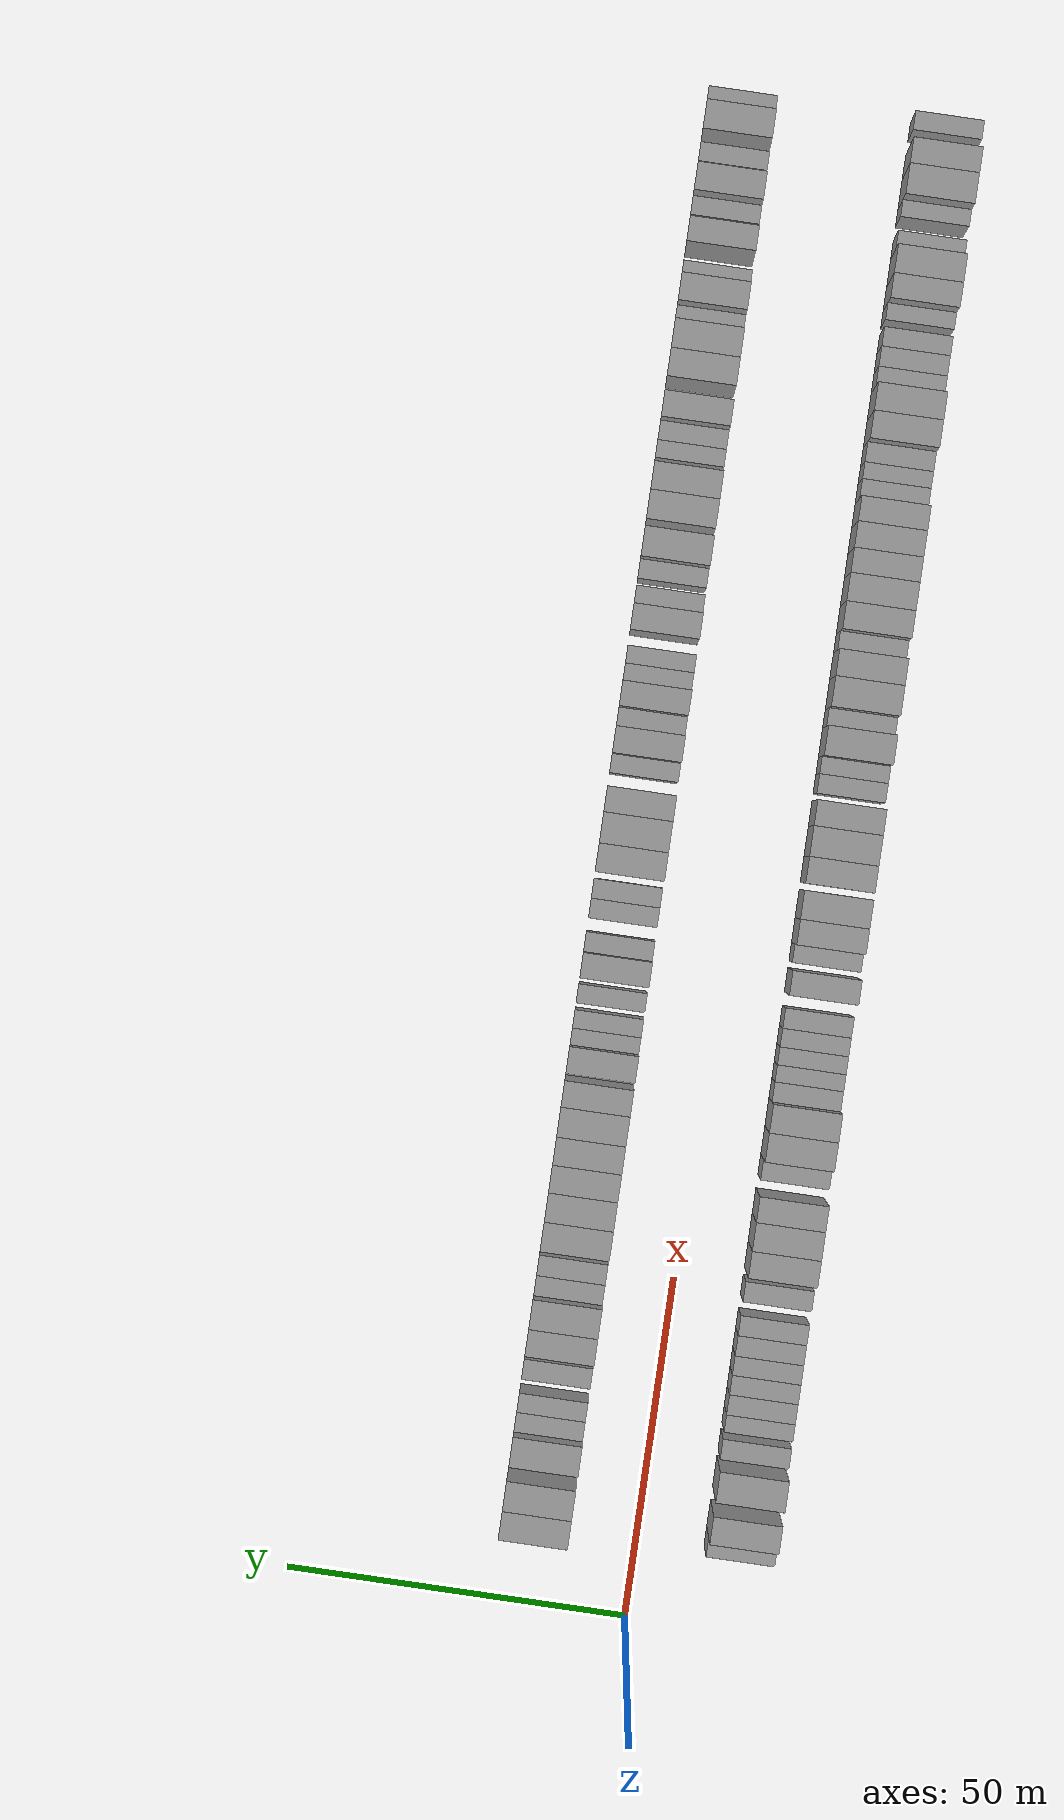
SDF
<sdf version="1.6">
 <world name="default">
  <scene>
   <sky><clouds><speed>12</speed></clouds></sky>
   <ambient>0.4 0.4 0.4 1</ambient>
   <background>0.7 0.7 0.7 1</background>
   <shadows>1</shadows>
  </scene>
  <gravity>0 0 -9.8066</gravity>
  <magnetic_field>6e-06 2.3e-05 -4.2e-05</magnetic_field>
  <physics default="0" name="default_physics" type="ode">
   <ode>
    <solver>
     <type>quick</type>
     <iters>10</iters>
     <sor>1.0</sor>
     <use_dynamic_moi_rescaling>0</use_dynamic_moi_rescaling>
    </solver>
    <constraints>
     <cfm>0</cfm>
     <erp>0.2</erp>
     <contact_max_correcting_vel>100</contact_max_correcting_vel>
     <contact_surface_layer>0.001</contact_surface_layer>
    </constraints>
   </ode>
   <max_step_size>0.004</max_step_size>
   <real_time_factor>1</real_time_factor>
   <real_time_update_rate>250</real_time_update_rate>
  </physics>
  <light name="sun" type="directional">
   <pose>0 0 10 0 0 0</pose>
   <diffuse>0.8 0.8 0.8 1</diffuse>
   <specular>0.2 0.2 0.2 1</specular>
   <attenuation>
    <range>1000</range>
    <constant>0.9</constant>
    <linear>0.01</linear>
    <quadratic>0.001</quadratic>
   </attenuation>
   <direction>-0.5 0.1 -0.9</direction>
  </light>
  <model name="building_1">
   <static>1</static>
   <pose>13.0584 15.0000 0 0.000000 0.000000 1.570796</pose>
   <link name="link">
    <pose>0 0 4.50 0 0 0</pose>
    <collision name="collision"><geometry><box><size>10.0000 4.1168 9.0000</size></box></geometry></collision>
    <visual name="visual">
     <cast_shadows>0</cast_shadows>
     <geometry><box><size>10.0000 4.1168 9.0000</size></box></geometry>
     <material>
      <script>
       <uri>model://grey_wall/materials/scripts</uri>
       <uri>model://grey_wall/materials/textures</uri>
       <name>vrc/grey_wall</name>
      </script>
     </material>
    </visual>
   </link>
  </model>
  <model name="building_2">
   <static>1</static>
   <pose>17.2955 15.0000 0 0.000000 0.000000 1.570796</pose>
   <link name="link">
    <pose>0 0 4.50 0 0 0</pose>
    <collision name="collision"><geometry><box><size>10.0000 4.3573 9.0000</size></box></geometry></collision>
    <visual name="visual">
     <cast_shadows>0</cast_shadows>
     <geometry><box><size>10.0000 4.3573 9.0000</size></box></geometry>
     <material>
      <script>
       <uri>model://grey_wall/materials/scripts</uri>
       <uri>model://grey_wall/materials/textures</uri>
       <name>vrc/grey_wall</name>
      </script>
     </material>
    </visual>
   </link>
  </model>
  <model name="building_3">
   <static>1</static>
   <pose>23.6623 15.0000 0 0.000000 0.000000 1.570796</pose>
   <link name="link">
    <pose>0 0 4.50 0 0 0</pose>
    <collision name="collision"><geometry><box><size>10.0000 4.3765 9.0000</size></box></geometry></collision>
    <visual name="visual">
     <cast_shadows>0</cast_shadows>
     <geometry><box><size>10.0000 4.3765 9.0000</size></box></geometry>
     <material>
      <script>
       <uri>model://grey_wall/materials/scripts</uri>
       <uri>model://grey_wall/materials/textures</uri>
       <name>vrc/grey_wall</name>
      </script>
     </material>
    </visual>
   </link>
  </model>
  <model name="building_4">
   <static>1</static>
   <pose>27.2714 15.0000 0 0.000000 0.000000 1.570796</pose>
   <link name="link">
    <pose>0 0 3.00 0 0 0</pose>
    <collision name="collision"><geometry><box><size>10.0000 2.8415 6.0000</size></box></geometry></collision>
    <visual name="visual">
     <cast_shadows>0</cast_shadows>
     <geometry><box><size>10.0000 2.8415 6.0000</size></box></geometry>
     <material>
      <script>
       <uri>model://grey_wall/materials/scripts</uri>
       <uri>model://grey_wall/materials/textures</uri>
       <name>vrc/grey_wall</name>
      </script>
     </material>
    </visual>
   </link>
  </model>
  <model name="building_5">
   <static>1</static>
   <pose>30.1008 15.0000 0 0.000000 0.000000 1.570796</pose>
   <link name="link">
    <pose>0 0 3.00 0 0 0</pose>
    <collision name="collision"><geometry><box><size>10.0000 2.8173 6.0000</size></box></geometry></collision>
    <visual name="visual">
     <cast_shadows>0</cast_shadows>
     <geometry><box><size>10.0000 2.8173 6.0000</size></box></geometry>
     <material>
      <script>
       <uri>model://grey_wall/materials/scripts</uri>
       <uri>model://grey_wall/materials/textures</uri>
       <name>vrc/grey_wall</name>
      </script>
     </material>
    </visual>
   </link>
  </model>
  <model name="building_6">
   <static>1</static>
   <pose>34.9873 15.0000 0 0.000000 0.000000 1.570796</pose>
   <link name="link">
    <pose>0 0 3.00 0 0 0</pose>
    <collision name="collision"><geometry><box><size>10.0000 2.9558 6.0000</size></box></geometry></collision>
    <visual name="visual">
     <cast_shadows>0</cast_shadows>
     <geometry><box><size>10.0000 2.9558 6.0000</size></box></geometry>
     <material>
      <script>
       <uri>model://grey_wall/materials/scripts</uri>
       <uri>model://grey_wall/materials/textures</uri>
       <name>vrc/grey_wall</name>
      </script>
     </material>
    </visual>
   </link>
  </model>
  <model name="building_7">
   <static>1</static>
   <pose>39.4198 15.0000 0 0.000000 0.000000 1.570796</pose>
   <link name="link">
    <pose>0 0 4.50 0 0 0</pose>
    <collision name="collision"><geometry><box><size>10.0000 3.9092 9.0000</size></box></geometry></collision>
    <visual name="visual">
     <cast_shadows>0</cast_shadows>
     <geometry><box><size>10.0000 3.9092 9.0000</size></box></geometry>
     <material>
      <script>
       <uri>model://grey_wall/materials/scripts</uri>
       <uri>model://grey_wall/materials/textures</uri>
       <name>vrc/grey_wall</name>
      </script>
     </material>
    </visual>
   </link>
  </model>
  <model name="building_8">
   <static>1</static>
   <pose>43.5342 15.0000 0 0.000000 0.000000 1.570796</pose>
   <link name="link">
    <pose>0 0 4.50 0 0 0</pose>
    <collision name="collision"><geometry><box><size>10.0000 4.3196 9.0000</size></box></geometry></collision>
    <visual name="visual">
     <cast_shadows>0</cast_shadows>
     <geometry><box><size>10.0000 4.3196 9.0000</size></box></geometry>
     <material>
      <script>
       <uri>model://grey_wall/materials/scripts</uri>
       <uri>model://grey_wall/materials/textures</uri>
       <name>vrc/grey_wall</name>
      </script>
     </material>
    </visual>
   </link>
  </model>
  <model name="building_9">
   <static>1</static>
   <pose>47.1552 15.0000 0 0.000000 0.000000 1.570796</pose>
   <link name="link">
    <pose>0 0 3.00 0 0 0</pose>
    <collision name="collision"><geometry><box><size>10.0000 2.9224 6.0000</size></box></geometry></collision>
    <visual name="visual">
     <cast_shadows>0</cast_shadows>
     <geometry><box><size>10.0000 2.9224 6.0000</size></box></geometry>
     <material>
      <script>
       <uri>model://grey_wall/materials/scripts</uri>
       <uri>model://grey_wall/materials/textures</uri>
       <name>vrc/grey_wall</name>
      </script>
     </material>
    </visual>
   </link>
  </model>
  <model name="building_10">
   <static>1</static>
   <pose>50.1067 15.0000 0 0.000000 0.000000 1.570796</pose>
   <link name="link">
    <pose>0 0 3.00 0 0 0</pose>
    <collision name="collision"><geometry><box><size>10.0000 2.9807 6.0000</size></box></geometry></collision>
    <visual name="visual">
     <cast_shadows>0</cast_shadows>
     <geometry><box><size>10.0000 2.9807 6.0000</size></box></geometry>
     <material>
      <script>
       <uri>model://grey_wall/materials/scripts</uri>
       <uri>model://grey_wall/materials/textures</uri>
       <name>vrc/grey_wall</name>
      </script>
     </material>
    </visual>
   </link>
  </model>
  <model name="building_11">
   <static>1</static>
   <pose>54.7344 15.0000 0 0.000000 0.000000 1.570796</pose>
   <link name="link">
    <pose>0 0 4.50 0 0 0</pose>
    <collision name="collision"><geometry><box><size>10.0000 4.2747 9.0000</size></box></geometry></collision>
    <visual name="visual">
     <cast_shadows>0</cast_shadows>
     <geometry><box><size>10.0000 4.2747 9.0000</size></box></geometry>
     <material>
      <script>
       <uri>model://grey_wall/materials/scripts</uri>
       <uri>model://grey_wall/materials/textures</uri>
       <name>vrc/grey_wall</name>
      </script>
     </material>
    </visual>
   </link>
  </model>
  <model name="building_12">
   <static>1</static>
   <pose>58.9776 15.0000 0 0.000000 0.000000 1.570796</pose>
   <link name="link">
    <pose>0 0 4.50 0 0 0</pose>
    <collision name="collision"><geometry><box><size>10.0000 4.2117 9.0000</size></box></geometry></collision>
    <visual name="visual">
     <cast_shadows>0</cast_shadows>
     <geometry><box><size>10.0000 4.2117 9.0000</size></box></geometry>
     <material>
      <script>
       <uri>model://grey_wall/materials/scripts</uri>
       <uri>model://grey_wall/materials/textures</uri>
       <name>vrc/grey_wall</name>
      </script>
     </material>
    </visual>
   </link>
  </model>
  <model name="building_13">
   <static>1</static>
   <pose>63.0904 15.0000 0 0.000000 0.000000 1.570796</pose>
   <link name="link">
    <pose>0 0 4.50 0 0 0</pose>
    <collision name="collision"><geometry><box><size>10.0000 4.0140 9.0000</size></box></geometry></collision>
    <visual name="visual">
     <cast_shadows>0</cast_shadows>
     <geometry><box><size>10.0000 4.0140 9.0000</size></box></geometry>
     <material>
      <script>
       <uri>model://grey_wall/materials/scripts</uri>
       <uri>model://grey_wall/materials/textures</uri>
       <name>vrc/grey_wall</name>
      </script>
     </material>
    </visual>
   </link>
  </model>
  <model name="building_14">
   <static>1</static>
   <pose>67.1182 15.0000 0 0.000000 0.000000 1.570796</pose>
   <link name="link">
    <pose>0 0 4.50 0 0 0</pose>
    <collision name="collision"><geometry><box><size>10.0000 4.0417 9.0000</size></box></geometry></collision>
    <visual name="visual">
     <cast_shadows>0</cast_shadows>
     <geometry><box><size>10.0000 4.0417 9.0000</size></box></geometry>
     <material>
      <script>
       <uri>model://grey_wall/materials/scripts</uri>
       <uri>model://grey_wall/materials/textures</uri>
       <name>vrc/grey_wall</name>
      </script>
     </material>
    </visual>
   </link>
  </model>
  <model name="building_15">
   <static>1</static>
   <pose>71.3008 15.0000 0 0.000000 0.000000 1.570796</pose>
   <link name="link">
    <pose>0 0 4.50 0 0 0</pose>
    <collision name="collision"><geometry><box><size>10.0000 4.3233 9.0000</size></box></geometry></collision>
    <visual name="visual">
     <cast_shadows>0</cast_shadows>
     <geometry><box><size>10.0000 4.3233 9.0000</size></box></geometry>
     <material>
      <script>
       <uri>model://grey_wall/materials/scripts</uri>
       <uri>model://grey_wall/materials/textures</uri>
       <name>vrc/grey_wall</name>
      </script>
     </material>
    </visual>
   </link>
  </model>
  <model name="building_16">
   <static>1</static>
   <pose>75.3823 15.0000 0 0.000000 0.000000 1.570796</pose>
   <link name="link">
    <pose>0 0 4.50 0 0 0</pose>
    <collision name="collision"><geometry><box><size>10.0000 3.8398 9.0000</size></box></geometry></collision>
    <visual name="visual">
     <cast_shadows>0</cast_shadows>
     <geometry><box><size>10.0000 3.8398 9.0000</size></box></geometry>
     <material>
      <script>
       <uri>model://grey_wall/materials/scripts</uri>
       <uri>model://grey_wall/materials/textures</uri>
       <name>vrc/grey_wall</name>
      </script>
     </material>
    </visual>
   </link>
  </model>
  <model name="building_17">
   <static>1</static>
   <pose>80.2570 15.0000 0 0.000000 0.000000 1.570796</pose>
   <link name="link">
    <pose>0 0 4.50 0 0 0</pose>
    <collision name="collision"><geometry><box><size>10.0000 3.9096 9.0000</size></box></geometry></collision>
    <visual name="visual">
     <cast_shadows>0</cast_shadows>
     <geometry><box><size>10.0000 3.9096 9.0000</size></box></geometry>
     <material>
      <script>
       <uri>model://grey_wall/materials/scripts</uri>
       <uri>model://grey_wall/materials/textures</uri>
       <name>vrc/grey_wall</name>
      </script>
     </material>
    </visual>
   </link>
  </model>
  <model name="building_18">
   <static>1</static>
   <pose>83.4359 15.0000 0 0.000000 0.000000 1.570796</pose>
   <link name="link">
    <pose>0 0 3.00 0 0 0</pose>
    <collision name="collision"><geometry><box><size>10.0000 2.4482 6.0000</size></box></geometry></collision>
    <visual name="visual">
     <cast_shadows>0</cast_shadows>
     <geometry><box><size>10.0000 2.4482 6.0000</size></box></geometry>
     <material>
      <script>
       <uri>model://grey_wall/materials/scripts</uri>
       <uri>model://grey_wall/materials/textures</uri>
       <name>vrc/grey_wall</name>
      </script>
     </material>
    </visual>
   </link>
  </model>
  <model name="building_19">
   <static>1</static>
   <pose>86.0006 15.0000 0 0.000000 0.000000 1.570796</pose>
   <link name="link">
    <pose>0 0 3.00 0 0 0</pose>
    <collision name="collision"><geometry><box><size>10.0000 2.6813 6.0000</size></box></geometry></collision>
    <visual name="visual">
     <cast_shadows>0</cast_shadows>
     <geometry><box><size>10.0000 2.6813 6.0000</size></box></geometry>
     <material>
      <script>
       <uri>model://grey_wall/materials/scripts</uri>
       <uri>model://grey_wall/materials/textures</uri>
       <name>vrc/grey_wall</name>
      </script>
     </material>
    </visual>
   </link>
  </model>
  <model name="building_20">
   <static>1</static>
   <pose>89.7267 15.0000 0 0.000000 0.000000 1.570796</pose>
   <link name="link">
    <pose>0 0 3.00 0 0 0</pose>
    <collision name="collision"><geometry><box><size>10.0000 2.7710 6.0000</size></box></geometry></collision>
    <visual name="visual">
     <cast_shadows>0</cast_shadows>
     <geometry><box><size>10.0000 2.7710 6.0000</size></box></geometry>
     <material>
      <script>
       <uri>model://grey_wall/materials/scripts</uri>
       <uri>model://grey_wall/materials/textures</uri>
       <name>vrc/grey_wall</name>
      </script>
     </material>
    </visual>
   </link>
  </model>
  <model name="building_21">
   <static>1</static>
   <pose>93.9495 15.0000 0 0.000000 0.000000 1.570796</pose>
   <link name="link">
    <pose>0 0 4.50 0 0 0</pose>
    <collision name="collision"><geometry><box><size>10.0000 3.6744 9.0000</size></box></geometry></collision>
    <visual name="visual">
     <cast_shadows>0</cast_shadows>
     <geometry><box><size>10.0000 3.6744 9.0000</size></box></geometry>
     <material>
      <script>
       <uri>model://grey_wall/materials/scripts</uri>
       <uri>model://grey_wall/materials/textures</uri>
       <name>vrc/grey_wall</name>
      </script>
     </material>
    </visual>
   </link>
  </model>
  <model name="building_22">
   <static>1</static>
   <pose>97.2493 15.0000 0 0.000000 0.000000 1.570796</pose>
   <link name="link">
    <pose>0 0 3.00 0 0 0</pose>
    <collision name="collision"><geometry><box><size>10.0000 2.9253 6.0000</size></box></geometry></collision>
    <visual name="visual">
     <cast_shadows>0</cast_shadows>
     <geometry><box><size>10.0000 2.9253 6.0000</size></box></geometry>
     <material>
      <script>
       <uri>model://grey_wall/materials/scripts</uri>
       <uri>model://grey_wall/materials/textures</uri>
       <name>vrc/grey_wall</name>
      </script>
     </material>
    </visual>
   </link>
  </model>
  <model name="building_23">
   <static>1</static>
   <pose>102.1418 15.0000 0 0.000000 0.000000 1.570796</pose>
   <link name="link">
    <pose>0 0 3.00 0 0 0</pose>
    <collision name="collision"><geometry><box><size>10.0000 2.8597 6.0000</size></box></geometry></collision>
    <visual name="visual">
     <cast_shadows>0</cast_shadows>
     <geometry><box><size>10.0000 2.8597 6.0000</size></box></geometry>
     <material>
      <script>
       <uri>model://grey_wall/materials/scripts</uri>
       <uri>model://grey_wall/materials/textures</uri>
       <name>vrc/grey_wall</name>
      </script>
     </material>
    </visual>
   </link>
  </model>
  <model name="building_24">
   <static>1</static>
   <pose>105.0148 15.0000 0 0.000000 0.000000 1.570796</pose>
   <link name="link">
    <pose>0 0 3.00 0 0 0</pose>
    <collision name="collision"><geometry><box><size>10.0000 2.8864 6.0000</size></box></geometry></collision>
    <visual name="visual">
     <cast_shadows>0</cast_shadows>
     <geometry><box><size>10.0000 2.8864 6.0000</size></box></geometry>
     <material>
      <script>
       <uri>model://grey_wall/materials/scripts</uri>
       <uri>model://grey_wall/materials/textures</uri>
       <name>vrc/grey_wall</name>
      </script>
     </material>
    </visual>
   </link>
  </model>
  <model name="building_25">
   <static>1</static>
   <pose>109.5327 15.0000 0 0.000000 0.000000 1.570796</pose>
   <link name="link">
    <pose>0 0 4.50 0 0 0</pose>
    <collision name="collision"><geometry><box><size>10.0000 4.1493 9.0000</size></box></geometry></collision>
    <visual name="visual">
     <cast_shadows>0</cast_shadows>
     <geometry><box><size>10.0000 4.1493 9.0000</size></box></geometry>
     <material>
      <script>
       <uri>model://grey_wall/materials/scripts</uri>
       <uri>model://grey_wall/materials/textures</uri>
       <name>vrc/grey_wall</name>
      </script>
     </material>
    </visual>
   </link>
  </model>
  <model name="building_26">
   <static>1</static>
   <pose>113.8534 15.0000 0 0.000000 0.000000 1.570796</pose>
   <link name="link">
    <pose>0 0 4.50 0 0 0</pose>
    <collision name="collision"><geometry><box><size>10.0000 4.4923 9.0000</size></box></geometry></collision>
    <visual name="visual">
     <cast_shadows>0</cast_shadows>
     <geometry><box><size>10.0000 4.4923 9.0000</size></box></geometry>
     <material>
      <script>
       <uri>model://grey_wall/materials/scripts</uri>
       <uri>model://grey_wall/materials/textures</uri>
       <name>vrc/grey_wall</name>
      </script>
     </material>
    </visual>
   </link>
  </model>
  <model name="building_27">
   <static>1</static>
   <pose>117.9723 15.0000 0 0.000000 0.000000 1.570796</pose>
   <link name="link">
    <pose>0 0 4.50 0 0 0</pose>
    <collision name="collision"><geometry><box><size>10.0000 3.7454 9.0000</size></box></geometry></collision>
    <visual name="visual">
     <cast_shadows>0</cast_shadows>
     <geometry><box><size>10.0000 3.7454 9.0000</size></box></geometry>
     <material>
      <script>
       <uri>model://grey_wall/materials/scripts</uri>
       <uri>model://grey_wall/materials/textures</uri>
       <name>vrc/grey_wall</name>
      </script>
     </material>
    </visual>
   </link>
  </model>
  <model name="building_28">
   <static>1</static>
   <pose>123.2405 15.0000 0 0.000000 0.000000 1.570796</pose>
   <link name="link">
    <pose>0 0 3.00 0 0 0</pose>
    <collision name="collision"><geometry><box><size>10.0000 2.7911 6.0000</size></box></geometry></collision>
    <visual name="visual">
     <cast_shadows>0</cast_shadows>
     <geometry><box><size>10.0000 2.7911 6.0000</size></box></geometry>
     <material>
      <script>
       <uri>model://grey_wall/materials/scripts</uri>
       <uri>model://grey_wall/materials/textures</uri>
       <name>vrc/grey_wall</name>
      </script>
     </material>
    </visual>
   </link>
  </model>
  <model name="building_29">
   <static>1</static>
   <pose>126.5817 15.0000 0 0.000000 0.000000 1.570796</pose>
   <link name="link">
    <pose>0 0 4.50 0 0 0</pose>
    <collision name="collision"><geometry><box><size>10.0000 3.8913 9.0000</size></box></geometry></collision>
    <visual name="visual">
     <cast_shadows>0</cast_shadows>
     <geometry><box><size>10.0000 3.8913 9.0000</size></box></geometry>
     <material>
      <script>
       <uri>model://grey_wall/materials/scripts</uri>
       <uri>model://grey_wall/materials/textures</uri>
       <name>vrc/grey_wall</name>
      </script>
     </material>
    </visual>
   </link>
  </model>
  <model name="building_30">
   <static>1</static>
   <pose>129.9661 15.0000 0 0.000000 0.000000 1.570796</pose>
   <link name="link">
    <pose>0 0 3.00 0 0 0</pose>
    <collision name="collision"><geometry><box><size>10.0000 2.8775 6.0000</size></box></geometry></collision>
    <visual name="visual">
     <cast_shadows>0</cast_shadows>
     <geometry><box><size>10.0000 2.8775 6.0000</size></box></geometry>
     <material>
      <script>
       <uri>model://grey_wall/materials/scripts</uri>
       <uri>model://grey_wall/materials/textures</uri>
       <name>vrc/grey_wall</name>
      </script>
     </material>
    </visual>
   </link>
  </model>
  <model name="building_31">
   <static>1</static>
   <pose>133.2513 15.0000 0 0.000000 0.000000 1.570796</pose>
   <link name="link">
    <pose>0 0 4.50 0 0 0</pose>
    <collision name="collision"><geometry><box><size>10.0000 3.6928 9.0000</size></box></geometry></collision>
    <visual name="visual">
     <cast_shadows>0</cast_shadows>
     <geometry><box><size>10.0000 3.6928 9.0000</size></box></geometry>
     <material>
      <script>
       <uri>model://grey_wall/materials/scripts</uri>
       <uri>model://grey_wall/materials/textures</uri>
       <name>vrc/grey_wall</name>
      </script>
     </material>
    </visual>
   </link>
  </model>
  <model name="building_32">
   <static>1</static>
   <pose>136.4618 15.0000 0 0.000000 0.000000 1.570796</pose>
   <link name="link">
    <pose>0 0 3.00 0 0 0</pose>
    <collision name="collision"><geometry><box><size>10.0000 2.7283 6.0000</size></box></geometry></collision>
    <visual name="visual">
     <cast_shadows>0</cast_shadows>
     <geometry><box><size>10.0000 2.7283 6.0000</size></box></geometry>
     <material>
      <script>
       <uri>model://grey_wall/materials/scripts</uri>
       <uri>model://grey_wall/materials/textures</uri>
       <name>vrc/grey_wall</name>
      </script>
     </material>
    </visual>
   </link>
  </model>
  <model name="building_33">
   <static>1</static>
   <pose>139.1239 15.0000 0 0.000000 0.000000 1.570796</pose>
   <link name="link">
    <pose>0 0 3.00 0 0 0</pose>
    <collision name="collision"><geometry><box><size>10.0000 2.5960 6.0000</size></box></geometry></collision>
    <visual name="visual">
     <cast_shadows>0</cast_shadows>
     <geometry><box><size>10.0000 2.5960 6.0000</size></box></geometry>
     <material>
      <script>
       <uri>model://grey_wall/materials/scripts</uri>
       <uri>model://grey_wall/materials/textures</uri>
       <name>vrc/grey_wall</name>
      </script>
     </material>
    </visual>
   </link>
  </model>
  <model name="building_34">
   <static>1</static>
   <pose>144.3345 15.0000 0 0.000000 0.000000 1.570796</pose>
   <link name="link">
    <pose>0 0 4.50 0 0 0</pose>
    <collision name="collision"><geometry><box><size>10.0000 3.8252 9.0000</size></box></geometry></collision>
    <visual name="visual">
     <cast_shadows>0</cast_shadows>
     <geometry><box><size>10.0000 3.8252 9.0000</size></box></geometry>
     <material>
      <script>
       <uri>model://grey_wall/materials/scripts</uri>
       <uri>model://grey_wall/materials/textures</uri>
       <name>vrc/grey_wall</name>
      </script>
     </material>
    </visual>
   </link>
  </model>
  <model name="building_35">
   <static>1</static>
   <pose>147.7011 15.0000 0 0.000000 0.000000 1.570796</pose>
   <link name="link">
    <pose>0 0 3.00 0 0 0</pose>
    <collision name="collision"><geometry><box><size>10.0000 2.9081 6.0000</size></box></geometry></collision>
    <visual name="visual">
     <cast_shadows>0</cast_shadows>
     <geometry><box><size>10.0000 2.9081 6.0000</size></box></geometry>
     <material>
      <script>
       <uri>model://grey_wall/materials/scripts</uri>
       <uri>model://grey_wall/materials/textures</uri>
       <name>vrc/grey_wall</name>
      </script>
     </material>
    </visual>
   </link>
  </model>
  <model name="building_36">
   <static>1</static>
   <pose>151.5841 15.0000 0 0.000000 0.000000 1.570796</pose>
   <link name="link">
    <pose>0 0 3.00 0 0 0</pose>
    <collision name="collision"><geometry><box><size>10.0000 2.8579 6.0000</size></box></geometry></collision>
    <visual name="visual">
     <cast_shadows>0</cast_shadows>
     <geometry><box><size>10.0000 2.8579 6.0000</size></box></geometry>
     <material>
      <script>
       <uri>model://grey_wall/materials/scripts</uri>
       <uri>model://grey_wall/materials/textures</uri>
       <name>vrc/grey_wall</name>
      </script>
     </material>
    </visual>
   </link>
  </model>
  <model name="building_37">
   <static>1</static>
   <pose>155.2118 15.0000 0 0.000000 0.000000 1.570796</pose>
   <link name="link">
    <pose>0 0 4.50 0 0 0</pose>
    <collision name="collision"><geometry><box><size>10.0000 4.3976 9.0000</size></box></geometry></collision>
    <visual name="visual">
     <cast_shadows>0</cast_shadows>
     <geometry><box><size>10.0000 4.3976 9.0000</size></box></geometry>
     <material>
      <script>
       <uri>model://grey_wall/materials/scripts</uri>
       <uri>model://grey_wall/materials/textures</uri>
       <name>vrc/grey_wall</name>
      </script>
     </material>
    </visual>
   </link>
  </model>
  <model name="building_38">
   <static>1</static>
   <pose>160.5394 15.0000 0 0.000000 0.000000 1.570796</pose>
   <link name="link">
    <pose>0 0 4.50 0 0 0</pose>
    <collision name="collision"><geometry><box><size>10.0000 4.2574 9.0000</size></box></geometry></collision>
    <visual name="visual">
     <cast_shadows>0</cast_shadows>
     <geometry><box><size>10.0000 4.2574 9.0000</size></box></geometry>
     <material>
      <script>
       <uri>model://grey_wall/materials/scripts</uri>
       <uri>model://grey_wall/materials/textures</uri>
       <name>vrc/grey_wall</name>
      </script>
     </material>
    </visual>
   </link>
  </model>
  <model name="building_39">
   <static>1</static>
   <pose>164.7098 15.0000 0 0.000000 0.000000 1.570796</pose>
   <link name="link">
    <pose>0 0 4.50 0 0 0</pose>
    <collision name="collision"><geometry><box><size>10.0000 4.0835 9.0000</size></box></geometry></collision>
    <visual name="visual">
     <cast_shadows>0</cast_shadows>
     <geometry><box><size>10.0000 4.0835 9.0000</size></box></geometry>
     <material>
      <script>
       <uri>model://grey_wall/materials/scripts</uri>
       <uri>model://grey_wall/materials/textures</uri>
       <name>vrc/grey_wall</name>
      </script>
     </material>
    </visual>
   </link>
  </model>
  <model name="building_40">
   <static>1</static>
   <pose>169.0527 15.0000 0 0.000000 0.000000 1.570796</pose>
   <link name="link">
    <pose>0 0 3.00 0 0 0</pose>
    <collision name="collision"><geometry><box><size>10.0000 2.6023 6.0000</size></box></geometry></collision>
    <visual name="visual">
     <cast_shadows>0</cast_shadows>
     <geometry><box><size>10.0000 2.6023 6.0000</size></box></geometry>
     <material>
      <script>
       <uri>model://grey_wall/materials/scripts</uri>
       <uri>model://grey_wall/materials/textures</uri>
       <name>vrc/grey_wall</name>
      </script>
     </material>
    </visual>
   </link>
  </model>
  <model name="building_41">
   <static>1</static>
   <pose>171.7632 15.0000 0 0.000000 0.000000 1.570796</pose>
   <link name="link">
    <pose>0 0 3.00 0 0 0</pose>
    <collision name="collision"><geometry><box><size>10.0000 2.8186 6.0000</size></box></geometry></collision>
    <visual name="visual">
     <cast_shadows>0</cast_shadows>
     <geometry><box><size>10.0000 2.8186 6.0000</size></box></geometry>
     <material>
      <script>
       <uri>model://grey_wall/materials/scripts</uri>
       <uri>model://grey_wall/materials/textures</uri>
       <name>vrc/grey_wall</name>
      </script>
     </material>
    </visual>
   </link>
  </model>
  <model name="building_42">
   <static>1</static>
   <pose>175.0899 15.0000 0 0.000000 0.000000 1.570796</pose>
   <link name="link">
    <pose>0 0 4.50 0 0 0</pose>
    <collision name="collision"><geometry><box><size>10.0000 3.8349 9.0000</size></box></geometry></collision>
    <visual name="visual">
     <cast_shadows>0</cast_shadows>
     <geometry><box><size>10.0000 3.8349 9.0000</size></box></geometry>
     <material>
      <script>
       <uri>model://grey_wall/materials/scripts</uri>
       <uri>model://grey_wall/materials/textures</uri>
       <name>vrc/grey_wall</name>
      </script>
     </material>
    </visual>
   </link>
  </model>
  <model name="building_43">
   <static>1</static>
   <pose>181.0642 15.0000 0 0.000000 0.000000 1.570796</pose>
   <link name="link">
    <pose>0 0 4.50 0 0 0</pose>
    <collision name="collision"><geometry><box><size>10.0000 4.1136 9.0000</size></box></geometry></collision>
    <visual name="visual">
     <cast_shadows>0</cast_shadows>
     <geometry><box><size>10.0000 4.1136 9.0000</size></box></geometry>
     <material>
      <script>
       <uri>model://grey_wall/materials/scripts</uri>
       <uri>model://grey_wall/materials/textures</uri>
       <name>vrc/grey_wall</name>
      </script>
     </material>
    </visual>
   </link>
  </model>
  <model name="building_44">
   <static>1</static>
   <pose>185.2542 15.0000 0 0.000000 0.000000 1.570796</pose>
   <link name="link">
    <pose>0 0 4.50 0 0 0</pose>
    <collision name="collision"><geometry><box><size>10.0000 4.2662 9.0000</size></box></geometry></collision>
    <visual name="visual">
     <cast_shadows>0</cast_shadows>
     <geometry><box><size>10.0000 4.2662 9.0000</size></box></geometry>
     <material>
      <script>
       <uri>model://grey_wall/materials/scripts</uri>
       <uri>model://grey_wall/materials/textures</uri>
       <name>vrc/grey_wall</name>
      </script>
     </material>
    </visual>
   </link>
  </model>
  <model name="building_45">
   <static>1</static>
   <pose>188.6804 15.0000 0 0.000000 0.000000 1.570796</pose>
   <link name="link">
    <pose>0 0 3.00 0 0 0</pose>
    <collision name="collision"><geometry><box><size>10.0000 2.5863 6.0000</size></box></geometry></collision>
    <visual name="visual">
     <cast_shadows>0</cast_shadows>
     <geometry><box><size>10.0000 2.5863 6.0000</size></box></geometry>
     <material>
      <script>
       <uri>model://grey_wall/materials/scripts</uri>
       <uri>model://grey_wall/materials/textures</uri>
       <name>vrc/grey_wall</name>
      </script>
     </material>
    </visual>
   </link>
  </model>
  <model name="building_46">
   <static>1</static>
   <pose>191.9830 15.0000 0 0.000000 0.000000 1.570796</pose>
   <link name="link">
    <pose>0 0 4.50 0 0 0</pose>
    <collision name="collision"><geometry><box><size>10.0000 4.0189 9.0000</size></box></geometry></collision>
    <visual name="visual">
     <cast_shadows>0</cast_shadows>
     <geometry><box><size>10.0000 4.0189 9.0000</size></box></geometry>
     <material>
      <script>
       <uri>model://grey_wall/materials/scripts</uri>
       <uri>model://grey_wall/materials/textures</uri>
       <name>vrc/grey_wall</name>
      </script>
     </material>
    </visual>
   </link>
  </model>
  <model name="building_47">
   <static>1</static>
   <pose>195.2415 15.0000 0 0.000000 0.000000 1.570796</pose>
   <link name="link">
    <pose>0 0 3.00 0 0 0</pose>
    <collision name="collision"><geometry><box><size>10.0000 2.4981 6.0000</size></box></geometry></collision>
    <visual name="visual">
     <cast_shadows>0</cast_shadows>
     <geometry><box><size>10.0000 2.4981 6.0000</size></box></geometry>
     <material>
      <script>
       <uri>model://grey_wall/materials/scripts</uri>
       <uri>model://grey_wall/materials/textures</uri>
       <name>vrc/grey_wall</name>
      </script>
     </material>
    </visual>
   </link>
  </model>
  <model name="building_48">
   <static>1</static>
   <pose>200.3131 15.0000 0 0.000000 0.000000 1.570796</pose>
   <link name="link">
    <pose>0 0 4.50 0 0 0</pose>
    <collision name="collision"><geometry><box><size>10.0000 3.6450 9.0000</size></box></geometry></collision>
    <visual name="visual">
     <cast_shadows>0</cast_shadows>
     <geometry><box><size>10.0000 3.6450 9.0000</size></box></geometry>
     <material>
      <script>
       <uri>model://grey_wall/materials/scripts</uri>
       <uri>model://grey_wall/materials/textures</uri>
       <name>vrc/grey_wall</name>
      </script>
     </material>
    </visual>
   </link>
  </model>
  <model name="building_49">
   <static>1</static>
   <pose>204.5103 15.0000 0 0.000000 0.000000 1.570796</pose>
   <link name="link">
    <pose>0 0 3.00 0 0 0</pose>
    <collision name="collision"><geometry><box><size>10.0000 2.7494 6.0000</size></box></geometry></collision>
    <visual name="visual">
     <cast_shadows>0</cast_shadows>
     <geometry><box><size>10.0000 2.7494 6.0000</size></box></geometry>
     <material>
      <script>
       <uri>model://grey_wall/materials/scripts</uri>
       <uri>model://grey_wall/materials/textures</uri>
       <name>vrc/grey_wall</name>
      </script>
     </material>
    </visual>
   </link>
  </model>
  <model name="building_50">
   <static>1</static>
   <pose>207.9162 15.0000 0 0.000000 0.000000 1.570796</pose>
   <link name="link">
    <pose>0 0 4.50 0 0 0</pose>
    <collision name="collision"><geometry><box><size>10.0000 4.0623 9.0000</size></box></geometry></collision>
    <visual name="visual">
     <cast_shadows>0</cast_shadows>
     <geometry><box><size>10.0000 4.0623 9.0000</size></box></geometry>
     <material>
      <script>
       <uri>model://grey_wall/materials/scripts</uri>
       <uri>model://grey_wall/materials/textures</uri>
       <name>vrc/grey_wall</name>
      </script>
     </material>
    </visual>
   </link>
  </model>
  <model name="building_51">
   <static>1</static>
   <pose>212.3395 15.0000 0 0.000000 0.000000 1.570796</pose>
   <link name="link">
    <pose>0 0 3.00 0 0 0</pose>
    <collision name="collision"><geometry><box><size>10.0000 2.7843 6.0000</size></box></geometry></collision>
    <visual name="visual">
     <cast_shadows>0</cast_shadows>
     <geometry><box><size>10.0000 2.7843 6.0000</size></box></geometry>
     <material>
      <script>
       <uri>model://grey_wall/materials/scripts</uri>
       <uri>model://grey_wall/materials/textures</uri>
       <name>vrc/grey_wall</name>
      </script>
     </material>
    </visual>
   </link>
  </model>
  <model name="building_52">
   <static>1</static>
   <pose>216.8495 15.0000 0 0.000000 0.000000 1.570796</pose>
   <link name="link">
    <pose>0 0 4.50 0 0 0</pose>
    <collision name="collision"><geometry><box><size>10.0000 4.2358 9.0000</size></box></geometry></collision>
    <visual name="visual">
     <cast_shadows>0</cast_shadows>
     <geometry><box><size>10.0000 4.2358 9.0000</size></box></geometry>
     <material>
      <script>
       <uri>model://grey_wall/materials/scripts</uri>
       <uri>model://grey_wall/materials/textures</uri>
       <name>vrc/grey_wall</name>
      </script>
     </material>
    </visual>
   </link>
  </model>
  <model name="building_53">
   <static>1</static>
   <pose>220.4136 15.0000 0 0.000000 0.000000 1.570796</pose>
   <link name="link">
    <pose>0 0 3.00 0 0 0</pose>
    <collision name="collision"><geometry><box><size>10.0000 2.8923 6.0000</size></box></geometry></collision>
    <visual name="visual">
     <cast_shadows>0</cast_shadows>
     <geometry><box><size>10.0000 2.8923 6.0000</size></box></geometry>
     <material>
      <script>
       <uri>model://grey_wall/materials/scripts</uri>
       <uri>model://grey_wall/materials/textures</uri>
       <name>vrc/grey_wall</name>
      </script>
     </material>
    </visual>
   </link>
  </model>
  <model name="building_54">
   <static>1</static>
   <pose>13.3420 -15.0000 0 0.000000 0.000000 1.570796</pose>
   <link name="link">
    <pose>0 0 3.00 0 0 0</pose>
    <collision name="collision"><geometry><box><size>10.0000 2.6839 6.0000</size></box></geometry></collision>
    <visual name="visual">
     <cast_shadows>0</cast_shadows>
     <geometry><box><size>10.0000 2.6839 6.0000</size></box></geometry>
     <material>
      <script>
       <uri>model://grey_wall/materials/scripts</uri>
       <uri>model://grey_wall/materials/textures</uri>
       <name>vrc/grey_wall</name>
      </script>
     </material>
    </visual>
   </link>
  </model>
  <model name="building_55">
   <static>1</static>
   <pose>16.6910 -15.0000 0 0.000000 0.000000 1.570796</pose>
   <link name="link">
    <pose>0 0 4.50 0 0 0</pose>
    <collision name="collision"><geometry><box><size>10.0000 4.0141 9.0000</size></box></geometry></collision>
    <visual name="visual">
     <cast_shadows>0</cast_shadows>
     <geometry><box><size>10.0000 4.0141 9.0000</size></box></geometry>
     <material>
      <script>
       <uri>model://grey_wall/materials/scripts</uri>
       <uri>model://grey_wall/materials/textures</uri>
       <name>vrc/grey_wall</name>
      </script>
     </material>
    </visual>
   </link>
  </model>
  <model name="building_56">
   <static>1</static>
   <pose>22.9406 -15.0000 0 0.000000 0.000000 1.570796</pose>
   <link name="link">
    <pose>0 0 4.50 0 0 0</pose>
    <collision name="collision"><geometry><box><size>10.0000 4.4851 9.0000</size></box></geometry></collision>
    <visual name="visual">
     <cast_shadows>0</cast_shadows>
     <geometry><box><size>10.0000 4.4851 9.0000</size></box></geometry>
     <material>
      <script>
       <uri>model://grey_wall/materials/scripts</uri>
       <uri>model://grey_wall/materials/textures</uri>
       <name>vrc/grey_wall</name>
      </script>
     </material>
    </visual>
   </link>
  </model>
  <model name="building_57">
   <static>1</static>
   <pose>27.6712 -15.0000 0 0.000000 0.000000 1.570796</pose>
   <link name="link">
    <pose>0 0 3.00 0 0 0</pose>
    <collision name="collision"><geometry><box><size>10.0000 2.9761 6.0000</size></box></geometry></collision>
    <visual name="visual">
     <cast_shadows>0</cast_shadows>
     <geometry><box><size>10.0000 2.9761 6.0000</size></box></geometry>
     <material>
      <script>
       <uri>model://grey_wall/materials/scripts</uri>
       <uri>model://grey_wall/materials/textures</uri>
       <name>vrc/grey_wall</name>
      </script>
     </material>
    </visual>
   </link>
  </model>
  <model name="building_58">
   <static>1</static>
   <pose>31.4191 -15.0000 0 0.000000 0.000000 1.570796</pose>
   <link name="link">
    <pose>0 0 3.00 0 0 0</pose>
    <collision name="collision"><geometry><box><size>10.0000 2.5198 6.0000</size></box></geometry></collision>
    <visual name="visual">
     <cast_shadows>0</cast_shadows>
     <geometry><box><size>10.0000 2.5198 6.0000</size></box></geometry>
     <material>
      <script>
       <uri>model://grey_wall/materials/scripts</uri>
       <uri>model://grey_wall/materials/textures</uri>
       <name>vrc/grey_wall</name>
      </script>
     </material>
    </visual>
   </link>
  </model>
  <model name="building_59">
   <static>1</static>
   <pose>34.1414 -15.0000 0 0.000000 0.000000 1.570796</pose>
   <link name="link">
    <pose>0 0 3.00 0 0 0</pose>
    <collision name="collision"><geometry><box><size>10.0000 2.9246 6.0000</size></box></geometry></collision>
    <visual name="visual">
     <cast_shadows>0</cast_shadows>
     <geometry><box><size>10.0000 2.9246 6.0000</size></box></geometry>
     <material>
      <script>
       <uri>model://grey_wall/materials/scripts</uri>
       <uri>model://grey_wall/materials/textures</uri>
       <name>vrc/grey_wall</name>
      </script>
     </material>
    </visual>
   </link>
  </model>
  <model name="building_60">
   <static>1</static>
   <pose>37.0262 -15.0000 0 0.000000 0.000000 1.570796</pose>
   <link name="link">
    <pose>0 0 3.00 0 0 0</pose>
    <collision name="collision"><geometry><box><size>10.0000 2.8450 6.0000</size></box></geometry></collision>
    <visual name="visual">
     <cast_shadows>0</cast_shadows>
     <geometry><box><size>10.0000 2.8450 6.0000</size></box></geometry>
     <material>
      <script>
       <uri>model://grey_wall/materials/scripts</uri>
       <uri>model://grey_wall/materials/textures</uri>
       <name>vrc/grey_wall</name>
      </script>
     </material>
    </visual>
   </link>
  </model>
  <model name="building_61">
   <static>1</static>
   <pose>39.8561 -15.0000 0 0.000000 0.000000 1.570796</pose>
   <link name="link">
    <pose>0 0 3.00 0 0 0</pose>
    <collision name="collision"><geometry><box><size>10.0000 2.8147 6.0000</size></box></geometry></collision>
    <visual name="visual">
     <cast_shadows>0</cast_shadows>
     <geometry><box><size>10.0000 2.8147 6.0000</size></box></geometry>
     <material>
      <script>
       <uri>model://grey_wall/materials/scripts</uri>
       <uri>model://grey_wall/materials/textures</uri>
       <name>vrc/grey_wall</name>
      </script>
     </material>
    </visual>
   </link>
  </model>
  <model name="building_62">
   <static>1</static>
   <pose>42.7350 -15.0000 0 0.000000 0.000000 1.570796</pose>
   <link name="link">
    <pose>0 0 3.00 0 0 0</pose>
    <collision name="collision"><geometry><box><size>10.0000 2.9431 6.0000</size></box></geometry></collision>
    <visual name="visual">
     <cast_shadows>0</cast_shadows>
     <geometry><box><size>10.0000 2.9431 6.0000</size></box></geometry>
     <material>
      <script>
       <uri>model://grey_wall/materials/scripts</uri>
       <uri>model://grey_wall/materials/textures</uri>
       <name>vrc/grey_wall</name>
      </script>
     </material>
    </visual>
   </link>
  </model>
  <model name="building_63">
   <static>1</static>
   <pose>45.6715 -15.0000 0 0.000000 0.000000 1.570796</pose>
   <link name="link">
    <pose>0 0 3.00 0 0 0</pose>
    <collision name="collision"><geometry><box><size>10.0000 2.9299 6.0000</size></box></geometry></collision>
    <visual name="visual">
     <cast_shadows>0</cast_shadows>
     <geometry><box><size>10.0000 2.9299 6.0000</size></box></geometry>
     <material>
      <script>
       <uri>model://grey_wall/materials/scripts</uri>
       <uri>model://grey_wall/materials/textures</uri>
       <name>vrc/grey_wall</name>
      </script>
     </material>
    </visual>
   </link>
  </model>
  <model name="building_64">
   <static>1</static>
   <pose>50.6182 -15.0000 0 0.000000 0.000000 1.570796</pose>
   <link name="link">
    <pose>0 0 3.00 0 0 0</pose>
    <collision name="collision"><geometry><box><size>10.0000 2.9634 6.0000</size></box></geometry></collision>
    <visual name="visual">
     <cast_shadows>0</cast_shadows>
     <geometry><box><size>10.0000 2.9634 6.0000</size></box></geometry>
     <material>
      <script>
       <uri>model://grey_wall/materials/scripts</uri>
       <uri>model://grey_wall/materials/textures</uri>
       <name>vrc/grey_wall</name>
      </script>
     </material>
    </visual>
   </link>
  </model>
  <model name="building_65">
   <static>1</static>
   <pose>55.0536 -15.0000 0 0.000000 0.000000 1.570796</pose>
   <link name="link">
    <pose>0 0 4.50 0 0 0</pose>
    <collision name="collision"><geometry><box><size>10.0000 3.9075 9.0000</size></box></geometry></collision>
    <visual name="visual">
     <cast_shadows>0</cast_shadows>
     <geometry><box><size>10.0000 3.9075 9.0000</size></box></geometry>
     <material>
      <script>
       <uri>model://grey_wall/materials/scripts</uri>
       <uri>model://grey_wall/materials/textures</uri>
       <name>vrc/grey_wall</name>
      </script>
     </material>
    </visual>
   </link>
  </model>
  <model name="building_66">
   <static>1</static>
   <pose>59.0808 -15.0000 0 0.000000 0.000000 1.570796</pose>
   <link name="link">
    <pose>0 0 4.50 0 0 0</pose>
    <collision name="collision"><geometry><box><size>10.0000 4.1467 9.0000</size></box></geometry></collision>
    <visual name="visual">
     <cast_shadows>0</cast_shadows>
     <geometry><box><size>10.0000 4.1467 9.0000</size></box></geometry>
     <material>
      <script>
       <uri>model://grey_wall/materials/scripts</uri>
       <uri>model://grey_wall/materials/textures</uri>
       <name>vrc/grey_wall</name>
      </script>
     </material>
    </visual>
   </link>
  </model>
  <model name="building_67">
   <static>1</static>
   <pose>63.0212 -15.0000 0 0.000000 0.000000 1.570796</pose>
   <link name="link">
    <pose>0 0 4.50 0 0 0</pose>
    <collision name="collision"><geometry><box><size>10.0000 3.7341 9.0000</size></box></geometry></collision>
    <visual name="visual">
     <cast_shadows>0</cast_shadows>
     <geometry><box><size>10.0000 3.7341 9.0000</size></box></geometry>
     <material>
      <script>
       <uri>model://grey_wall/materials/scripts</uri>
       <uri>model://grey_wall/materials/textures</uri>
       <name>vrc/grey_wall</name>
      </script>
     </material>
    </visual>
   </link>
  </model>
  <model name="building_68">
   <static>1</static>
   <pose>68.3799 -15.0000 0 0.000000 0.000000 1.570796</pose>
   <link name="link">
    <pose>0 0 3.00 0 0 0</pose>
    <collision name="collision"><geometry><box><size>10.0000 2.9834 6.0000</size></box></geometry></collision>
    <visual name="visual">
     <cast_shadows>0</cast_shadows>
     <geometry><box><size>10.0000 2.9834 6.0000</size></box></geometry>
     <material>
      <script>
       <uri>model://grey_wall/materials/scripts</uri>
       <uri>model://grey_wall/materials/textures</uri>
       <name>vrc/grey_wall</name>
      </script>
     </material>
    </visual>
   </link>
  </model>
  <model name="building_69">
   <static>1</static>
   <pose>71.9738 -15.0000 0 0.000000 0.000000 1.570796</pose>
   <link name="link">
    <pose>0 0 4.50 0 0 0</pose>
    <collision name="collision"><geometry><box><size>10.0000 4.2044 9.0000</size></box></geometry></collision>
    <visual name="visual">
     <cast_shadows>0</cast_shadows>
     <geometry><box><size>10.0000 4.2044 9.0000</size></box></geometry>
     <material>
      <script>
       <uri>model://grey_wall/materials/scripts</uri>
       <uri>model://grey_wall/materials/textures</uri>
       <name>vrc/grey_wall</name>
      </script>
     </material>
    </visual>
   </link>
  </model>
  <model name="building_70">
   <static>1</static>
   <pose>76.1509 -15.0000 0 0.000000 0.000000 1.570796</pose>
   <link name="link">
    <pose>0 0 4.50 0 0 0</pose>
    <collision name="collision"><geometry><box><size>10.0000 4.1498 9.0000</size></box></geometry></collision>
    <visual name="visual">
     <cast_shadows>0</cast_shadows>
     <geometry><box><size>10.0000 4.1498 9.0000</size></box></geometry>
     <material>
      <script>
       <uri>model://grey_wall/materials/scripts</uri>
       <uri>model://grey_wall/materials/textures</uri>
       <name>vrc/grey_wall</name>
      </script>
     </material>
    </visual>
   </link>
  </model>
  <model name="building_71">
   <static>1</static>
   <pose>79.6998 -15.0000 0 0.000000 0.000000 1.570796</pose>
   <link name="link">
    <pose>0 0 3.00 0 0 0</pose>
    <collision name="collision"><geometry><box><size>10.0000 2.9479 6.0000</size></box></geometry></collision>
    <visual name="visual">
     <cast_shadows>0</cast_shadows>
     <geometry><box><size>10.0000 2.9479 6.0000</size></box></geometry>
     <material>
      <script>
       <uri>model://grey_wall/materials/scripts</uri>
       <uri>model://grey_wall/materials/textures</uri>
       <name>vrc/grey_wall</name>
      </script>
     </material>
    </visual>
   </link>
  </model>
  <model name="building_72">
   <static>1</static>
   <pose>82.4166 -15.0000 0 0.000000 0.000000 1.570796</pose>
   <link name="link">
    <pose>0 0 3.00 0 0 0</pose>
    <collision name="collision"><geometry><box><size>10.0000 2.4856 6.0000</size></box></geometry></collision>
    <visual name="visual">
     <cast_shadows>0</cast_shadows>
     <geometry><box><size>10.0000 2.4856 6.0000</size></box></geometry>
     <material>
      <script>
       <uri>model://grey_wall/materials/scripts</uri>
       <uri>model://grey_wall/materials/textures</uri>
       <name>vrc/grey_wall</name>
      </script>
     </material>
    </visual>
   </link>
  </model>
  <model name="building_73">
   <static>1</static>
   <pose>84.9606 -15.0000 0 0.000000 0.000000 1.570796</pose>
   <link name="link">
    <pose>0 0 3.00 0 0 0</pose>
    <collision name="collision"><geometry><box><size>10.0000 2.6024 6.0000</size></box></geometry></collision>
    <visual name="visual">
     <cast_shadows>0</cast_shadows>
     <geometry><box><size>10.0000 2.6024 6.0000</size></box></geometry>
     <material>
      <script>
       <uri>model://grey_wall/materials/scripts</uri>
       <uri>model://grey_wall/materials/textures</uri>
       <name>vrc/grey_wall</name>
      </script>
     </material>
    </visual>
   </link>
  </model>
  <model name="building_74">
   <static>1</static>
   <pose>87.6168 -15.0000 0 0.000000 0.000000 1.570796</pose>
   <link name="link">
    <pose>0 0 3.00 0 0 0</pose>
    <collision name="collision"><geometry><box><size>10.0000 2.7101 6.0000</size></box></geometry></collision>
    <visual name="visual">
     <cast_shadows>0</cast_shadows>
     <geometry><box><size>10.0000 2.7101 6.0000</size></box></geometry>
     <material>
      <script>
       <uri>model://grey_wall/materials/scripts</uri>
       <uri>model://grey_wall/materials/textures</uri>
       <name>vrc/grey_wall</name>
      </script>
     </material>
    </visual>
   </link>
  </model>
  <model name="building_75">
   <static>1</static>
   <pose>90.4583 -15.0000 0 0.000000 0.000000 1.570796</pose>
   <link name="link">
    <pose>0 0 3.00 0 0 0</pose>
    <collision name="collision"><geometry><box><size>10.0000 2.9728 6.0000</size></box></geometry></collision>
    <visual name="visual">
     <cast_shadows>0</cast_shadows>
     <geometry><box><size>10.0000 2.9728 6.0000</size></box></geometry>
     <material>
      <script>
       <uri>model://grey_wall/materials/scripts</uri>
       <uri>model://grey_wall/materials/textures</uri>
       <name>vrc/grey_wall</name>
      </script>
     </material>
    </visual>
   </link>
  </model>
  <model name="building_76">
   <static>1</static>
   <pose>95.7457 -15.0000 0 0.000000 0.000000 1.570796</pose>
   <link name="link">
    <pose>0 0 4.50 0 0 0</pose>
    <collision name="collision"><geometry><box><size>10.0000 3.6021 9.0000</size></box></geometry></collision>
    <visual name="visual">
     <cast_shadows>0</cast_shadows>
     <geometry><box><size>10.0000 3.6021 9.0000</size></box></geometry>
     <material>
      <script>
       <uri>model://grey_wall/materials/scripts</uri>
       <uri>model://grey_wall/materials/textures</uri>
       <name>vrc/grey_wall</name>
      </script>
     </material>
    </visual>
   </link>
  </model>
  <model name="building_77">
   <static>1</static>
   <pose>99.8922 -15.0000 0 0.000000 0.000000 1.570796</pose>
   <link name="link">
    <pose>0 0 3.00 0 0 0</pose>
    <collision name="collision"><geometry><box><size>10.0000 2.6910 6.0000</size></box></geometry></collision>
    <visual name="visual">
     <cast_shadows>0</cast_shadows>
     <geometry><box><size>10.0000 2.6910 6.0000</size></box></geometry>
     <material>
      <script>
       <uri>model://grey_wall/materials/scripts</uri>
       <uri>model://grey_wall/materials/textures</uri>
       <name>vrc/grey_wall</name>
      </script>
     </material>
    </visual>
   </link>
  </model>
  <model name="building_78">
   <static>1</static>
   <pose>103.0902 -15.0000 0 0.000000 0.000000 1.570796</pose>
   <link name="link">
    <pose>0 0 4.50 0 0 0</pose>
    <collision name="collision"><geometry><box><size>10.0000 3.7051 9.0000</size></box></geometry></collision>
    <visual name="visual">
     <cast_shadows>0</cast_shadows>
     <geometry><box><size>10.0000 3.7051 9.0000</size></box></geometry>
     <material>
      <script>
       <uri>model://grey_wall/materials/scripts</uri>
       <uri>model://grey_wall/materials/textures</uri>
       <name>vrc/grey_wall</name>
      </script>
     </material>
    </visual>
   </link>
  </model>
  <model name="building_79">
   <static>1</static>
   <pose>107.0325 -15.0000 0 0.000000 0.000000 1.570796</pose>
   <link name="link">
    <pose>0 0 4.50 0 0 0</pose>
    <collision name="collision"><geometry><box><size>10.0000 4.1794 9.0000</size></box></geometry></collision>
    <visual name="visual">
     <cast_shadows>0</cast_shadows>
     <geometry><box><size>10.0000 4.1794 9.0000</size></box></geometry>
     <material>
      <script>
       <uri>model://grey_wall/materials/scripts</uri>
       <uri>model://grey_wall/materials/textures</uri>
       <name>vrc/grey_wall</name>
      </script>
     </material>
    </visual>
   </link>
  </model>
  <model name="building_80">
   <static>1</static>
   <pose>112.0677 -15.0000 0 0.000000 0.000000 1.570796</pose>
   <link name="link">
    <pose>0 0 4.50 0 0 0</pose>
    <collision name="collision"><geometry><box><size>10.0000 3.8910 9.0000</size></box></geometry></collision>
    <visual name="visual">
     <cast_shadows>0</cast_shadows>
     <geometry><box><size>10.0000 3.8910 9.0000</size></box></geometry>
     <material>
      <script>
       <uri>model://grey_wall/materials/scripts</uri>
       <uri>model://grey_wall/materials/textures</uri>
       <name>vrc/grey_wall</name>
      </script>
     </material>
    </visual>
   </link>
  </model>
  <model name="building_81">
   <static>1</static>
   <pose>116.2319 -15.0000 0 0.000000 0.000000 1.570796</pose>
   <link name="link">
    <pose>0 0 4.50 0 0 0</pose>
    <collision name="collision"><geometry><box><size>10.0000 4.4374 9.0000</size></box></geometry></collision>
    <visual name="visual">
     <cast_shadows>0</cast_shadows>
     <geometry><box><size>10.0000 4.4374 9.0000</size></box></geometry>
     <material>
      <script>
       <uri>model://grey_wall/materials/scripts</uri>
       <uri>model://grey_wall/materials/textures</uri>
       <name>vrc/grey_wall</name>
      </script>
     </material>
    </visual>
   </link>
  </model>
  <model name="building_82">
   <static>1</static>
   <pose>120.3275 -15.0000 0 0.000000 0.000000 1.570796</pose>
   <link name="link">
    <pose>0 0 4.50 0 0 0</pose>
    <collision name="collision"><geometry><box><size>10.0000 3.7538 9.0000</size></box></geometry></collision>
    <visual name="visual">
     <cast_shadows>0</cast_shadows>
     <geometry><box><size>10.0000 3.7538 9.0000</size></box></geometry>
     <material>
      <script>
       <uri>model://grey_wall/materials/scripts</uri>
       <uri>model://grey_wall/materials/textures</uri>
       <name>vrc/grey_wall</name>
      </script>
     </material>
    </visual>
   </link>
  </model>
  <model name="building_83">
   <static>1</static>
   <pose>124.6297 -15.0000 0 0.000000 0.000000 1.570796</pose>
   <link name="link">
    <pose>0 0 3.00 0 0 0</pose>
    <collision name="collision"><geometry><box><size>10.0000 2.8504 6.0000</size></box></geometry></collision>
    <visual name="visual">
     <cast_shadows>0</cast_shadows>
     <geometry><box><size>10.0000 2.8504 6.0000</size></box></geometry>
     <material>
      <script>
       <uri>model://grey_wall/materials/scripts</uri>
       <uri>model://grey_wall/materials/textures</uri>
       <name>vrc/grey_wall</name>
      </script>
     </material>
    </visual>
   </link>
  </model>
  <model name="building_84">
   <static>1</static>
   <pose>127.3165 -15.0000 0 0.000000 0.000000 1.570796</pose>
   <link name="link">
    <pose>0 0 3.00 0 0 0</pose>
    <collision name="collision"><geometry><box><size>10.0000 2.5233 6.0000</size></box></geometry></collision>
    <visual name="visual">
     <cast_shadows>0</cast_shadows>
     <geometry><box><size>10.0000 2.5233 6.0000</size></box></geometry>
     <material>
      <script>
       <uri>model://grey_wall/materials/scripts</uri>
       <uri>model://grey_wall/materials/textures</uri>
       <name>vrc/grey_wall</name>
      </script>
     </material>
    </visual>
   </link>
  </model>
  <model name="building_85">
   <static>1</static>
   <pose>130.7624 -15.0000 0 0.000000 0.000000 1.570796</pose>
   <link name="link">
    <pose>0 0 4.50 0 0 0</pose>
    <collision name="collision"><geometry><box><size>10.0000 4.3685 9.0000</size></box></geometry></collision>
    <visual name="visual">
     <cast_shadows>0</cast_shadows>
     <geometry><box><size>10.0000 4.3685 9.0000</size></box></geometry>
     <material>
      <script>
       <uri>model://grey_wall/materials/scripts</uri>
       <uri>model://grey_wall/materials/textures</uri>
       <name>vrc/grey_wall</name>
      </script>
     </material>
    </visual>
   </link>
  </model>
  <model name="building_86">
   <static>1</static>
   <pose>134.3047 -15.0000 0 0.000000 0.000000 1.570796</pose>
   <link name="link">
    <pose>0 0 3.00 0 0 0</pose>
    <collision name="collision"><geometry><box><size>10.0000 2.7161 6.0000</size></box></geometry></collision>
    <visual name="visual">
     <cast_shadows>0</cast_shadows>
     <geometry><box><size>10.0000 2.7161 6.0000</size></box></geometry>
     <material>
      <script>
       <uri>model://grey_wall/materials/scripts</uri>
       <uri>model://grey_wall/materials/textures</uri>
       <name>vrc/grey_wall</name>
      </script>
     </material>
    </visual>
   </link>
  </model>
  <model name="building_87">
   <static>1</static>
   <pose>137.8798 -15.0000 0 0.000000 0.000000 1.570796</pose>
   <link name="link">
    <pose>0 0 4.50 0 0 0</pose>
    <collision name="collision"><geometry><box><size>10.0000 4.4342 9.0000</size></box></geometry></collision>
    <visual name="visual">
     <cast_shadows>0</cast_shadows>
     <geometry><box><size>10.0000 4.4342 9.0000</size></box></geometry>
     <material>
      <script>
       <uri>model://grey_wall/materials/scripts</uri>
       <uri>model://grey_wall/materials/textures</uri>
       <name>vrc/grey_wall</name>
      </script>
     </material>
    </visual>
   </link>
  </model>
  <model name="building_88">
   <static>1</static>
   <pose>142.0542 -15.0000 0 0.000000 0.000000 1.570796</pose>
   <link name="link">
    <pose>0 0 4.50 0 0 0</pose>
    <collision name="collision"><geometry><box><size>10.0000 3.9146 9.0000</size></box></geometry></collision>
    <visual name="visual">
     <cast_shadows>0</cast_shadows>
     <geometry><box><size>10.0000 3.9146 9.0000</size></box></geometry>
     <material>
      <script>
       <uri>model://grey_wall/materials/scripts</uri>
       <uri>model://grey_wall/materials/textures</uri>
       <name>vrc/grey_wall</name>
      </script>
     </material>
    </visual>
   </link>
  </model>
  <model name="building_89">
   <static>1</static>
   <pose>145.4409 -15.0000 0 0.000000 0.000000 1.570796</pose>
   <link name="link">
    <pose>0 0 3.00 0 0 0</pose>
    <collision name="collision"><geometry><box><size>10.0000 2.8587 6.0000</size></box></geometry></collision>
    <visual name="visual">
     <cast_shadows>0</cast_shadows>
     <geometry><box><size>10.0000 2.8587 6.0000</size></box></geometry>
     <material>
      <script>
       <uri>model://grey_wall/materials/scripts</uri>
       <uri>model://grey_wall/materials/textures</uri>
       <name>vrc/grey_wall</name>
      </script>
     </material>
    </visual>
   </link>
  </model>
  <model name="building_90">
   <static>1</static>
   <pose>148.8855 -15.0000 0 0.000000 0.000000 1.570796</pose>
   <link name="link">
    <pose>0 0 4.50 0 0 0</pose>
    <collision name="collision"><geometry><box><size>10.0000 4.0306 9.0000</size></box></geometry></collision>
    <visual name="visual">
     <cast_shadows>0</cast_shadows>
     <geometry><box><size>10.0000 4.0306 9.0000</size></box></geometry>
     <material>
      <script>
       <uri>model://grey_wall/materials/scripts</uri>
       <uri>model://grey_wall/materials/textures</uri>
       <name>vrc/grey_wall</name>
      </script>
     </material>
    </visual>
   </link>
  </model>
  <model name="building_91">
   <static>1</static>
   <pose>152.9528 -15.0000 0 0.000000 0.000000 1.570796</pose>
   <link name="link">
    <pose>0 0 4.50 0 0 0</pose>
    <collision name="collision"><geometry><box><size>10.0000 4.1041 9.0000</size></box></geometry></collision>
    <visual name="visual">
     <cast_shadows>0</cast_shadows>
     <geometry><box><size>10.0000 4.1041 9.0000</size></box></geometry>
     <material>
      <script>
       <uri>model://grey_wall/materials/scripts</uri>
       <uri>model://grey_wall/materials/textures</uri>
       <name>vrc/grey_wall</name>
      </script>
     </material>
    </visual>
   </link>
  </model>
  <model name="building_92">
   <static>1</static>
   <pose>156.8177 -15.0000 0 0.000000 0.000000 1.570796</pose>
   <link name="link">
    <pose>0 0 4.50 0 0 0</pose>
    <collision name="collision"><geometry><box><size>10.0000 3.6257 9.0000</size></box></geometry></collision>
    <visual name="visual">
     <cast_shadows>0</cast_shadows>
     <geometry><box><size>10.0000 3.6257 9.0000</size></box></geometry>
     <material>
      <script>
       <uri>model://grey_wall/materials/scripts</uri>
       <uri>model://grey_wall/materials/textures</uri>
       <name>vrc/grey_wall</name>
      </script>
     </material>
    </visual>
   </link>
  </model>
  <model name="building_93">
   <static>1</static>
   <pose>160.5381 -15.0000 0 0.000000 0.000000 1.570796</pose>
   <link name="link">
    <pose>0 0 4.50 0 0 0</pose>
    <collision name="collision"><geometry><box><size>10.0000 3.8152 9.0000</size></box></geometry></collision>
    <visual name="visual">
     <cast_shadows>0</cast_shadows>
     <geometry><box><size>10.0000 3.8152 9.0000</size></box></geometry>
     <material>
      <script>
       <uri>model://grey_wall/materials/scripts</uri>
       <uri>model://grey_wall/materials/textures</uri>
       <name>vrc/grey_wall</name>
      </script>
     </material>
    </visual>
   </link>
  </model>
  <model name="building_94">
   <static>1</static>
   <pose>164.2671 -15.0000 0 0.000000 0.000000 1.570796</pose>
   <link name="link">
    <pose>0 0 4.50 0 0 0</pose>
    <collision name="collision"><geometry><box><size>10.0000 3.6428 9.0000</size></box></geometry></collision>
    <visual name="visual">
     <cast_shadows>0</cast_shadows>
     <geometry><box><size>10.0000 3.6428 9.0000</size></box></geometry>
     <material>
      <script>
       <uri>model://grey_wall/materials/scripts</uri>
       <uri>model://grey_wall/materials/textures</uri>
       <name>vrc/grey_wall</name>
      </script>
     </material>
    </visual>
   </link>
  </model>
  <model name="building_95">
   <static>1</static>
   <pose>167.5552 -15.0000 0 0.000000 0.000000 1.570796</pose>
   <link name="link">
    <pose>0 0 3.00 0 0 0</pose>
    <collision name="collision"><geometry><box><size>10.0000 2.9334 6.0000</size></box></geometry></collision>
    <visual name="visual">
     <cast_shadows>0</cast_shadows>
     <geometry><box><size>10.0000 2.9334 6.0000</size></box></geometry>
     <material>
      <script>
       <uri>model://grey_wall/materials/scripts</uri>
       <uri>model://grey_wall/materials/textures</uri>
       <name>vrc/grey_wall</name>
      </script>
     </material>
    </visual>
   </link>
  </model>
  <model name="building_96">
   <static>1</static>
   <pose>170.2436 -15.0000 0 0.000000 0.000000 1.570796</pose>
   <link name="link">
    <pose>0 0 3.00 0 0 0</pose>
    <collision name="collision"><geometry><box><size>10.0000 2.4434 6.0000</size></box></geometry></collision>
    <visual name="visual">
     <cast_shadows>0</cast_shadows>
     <geometry><box><size>10.0000 2.4434 6.0000</size></box></geometry>
     <material>
      <script>
       <uri>model://grey_wall/materials/scripts</uri>
       <uri>model://grey_wall/materials/textures</uri>
       <name>vrc/grey_wall</name>
      </script>
     </material>
    </visual>
   </link>
  </model>
  <model name="building_97">
   <static>1</static>
   <pose>172.9290 -15.0000 0 0.000000 0.000000 1.570796</pose>
   <link name="link">
    <pose>0 0 3.00 0 0 0</pose>
    <collision name="collision"><geometry><box><size>10.0000 2.9273 6.0000</size></box></geometry></collision>
    <visual name="visual">
     <cast_shadows>0</cast_shadows>
     <geometry><box><size>10.0000 2.9273 6.0000</size></box></geometry>
     <material>
      <script>
       <uri>model://grey_wall/materials/scripts</uri>
       <uri>model://grey_wall/materials/textures</uri>
       <name>vrc/grey_wall</name>
      </script>
     </material>
    </visual>
   </link>
  </model>
  <model name="building_98">
   <static>1</static>
   <pose>176.4029 -15.0000 0 0.000000 0.000000 1.570796</pose>
   <link name="link">
    <pose>0 0 4.50 0 0 0</pose>
    <collision name="collision"><geometry><box><size>10.0000 4.0204 9.0000</size></box></geometry></collision>
    <visual name="visual">
     <cast_shadows>0</cast_shadows>
     <geometry><box><size>10.0000 4.0204 9.0000</size></box></geometry>
     <material>
      <script>
       <uri>model://grey_wall/materials/scripts</uri>
       <uri>model://grey_wall/materials/textures</uri>
       <name>vrc/grey_wall</name>
      </script>
     </material>
    </visual>
   </link>
  </model>
  <model name="building_99">
   <static>1</static>
   <pose>180.4525 -15.0000 0 0.000000 0.000000 1.570796</pose>
   <link name="link">
    <pose>0 0 4.50 0 0 0</pose>
    <collision name="collision"><geometry><box><size>10.0000 4.0789 9.0000</size></box></geometry></collision>
    <visual name="visual">
     <cast_shadows>0</cast_shadows>
     <geometry><box><size>10.0000 4.0789 9.0000</size></box></geometry>
     <material>
      <script>
       <uri>model://grey_wall/materials/scripts</uri>
       <uri>model://grey_wall/materials/textures</uri>
       <name>vrc/grey_wall</name>
      </script>
     </material>
    </visual>
   </link>
  </model>
  <model name="building_100">
   <static>1</static>
   <pose>183.9404 -15.0000 0 0.000000 0.000000 1.570796</pose>
   <link name="link">
    <pose>0 0 3.00 0 0 0</pose>
    <collision name="collision"><geometry><box><size>10.0000 2.8969 6.0000</size></box></geometry></collision>
    <visual name="visual">
     <cast_shadows>0</cast_shadows>
     <geometry><box><size>10.0000 2.8969 6.0000</size></box></geometry>
     <material>
      <script>
       <uri>model://grey_wall/materials/scripts</uri>
       <uri>model://grey_wall/materials/textures</uri>
       <name>vrc/grey_wall</name>
      </script>
     </material>
    </visual>
   </link>
  </model>
  <model name="building_101">
   <static>1</static>
   <pose>186.8614 -15.0000 0 0.000000 0.000000 1.570796</pose>
   <link name="link">
    <pose>0 0 3.00 0 0 0</pose>
    <collision name="collision"><geometry><box><size>10.0000 2.9450 6.0000</size></box></geometry></collision>
    <visual name="visual">
     <cast_shadows>0</cast_shadows>
     <geometry><box><size>10.0000 2.9450 6.0000</size></box></geometry>
     <material>
      <script>
       <uri>model://grey_wall/materials/scripts</uri>
       <uri>model://grey_wall/materials/textures</uri>
       <name>vrc/grey_wall</name>
      </script>
     </material>
    </visual>
   </link>
  </model>
  <model name="building_102">
   <static>1</static>
   <pose>189.7482 -15.0000 0 0.000000 0.000000 1.570796</pose>
   <link name="link">
    <pose>0 0 3.00 0 0 0</pose>
    <collision name="collision"><geometry><box><size>10.0000 2.8286 6.0000</size></box></geometry></collision>
    <visual name="visual">
     <cast_shadows>0</cast_shadows>
     <geometry><box><size>10.0000 2.8286 6.0000</size></box></geometry>
     <material>
      <script>
       <uri>model://grey_wall/materials/scripts</uri>
       <uri>model://grey_wall/materials/textures</uri>
       <name>vrc/grey_wall</name>
      </script>
     </material>
    </visual>
   </link>
  </model>
  <model name="building_103">
   <static>1</static>
   <pose>193.3975 -15.0000 0 0.000000 0.000000 1.570796</pose>
   <link name="link">
    <pose>0 0 3.00 0 0 0</pose>
    <collision name="collision"><geometry><box><size>10.0000 2.4700 6.0000</size></box></geometry></collision>
    <visual name="visual">
     <cast_shadows>0</cast_shadows>
     <geometry><box><size>10.0000 2.4700 6.0000</size></box></geometry>
     <material>
      <script>
       <uri>model://grey_wall/materials/scripts</uri>
       <uri>model://grey_wall/materials/textures</uri>
       <name>vrc/grey_wall</name>
      </script>
     </material>
    </visual>
   </link>
  </model>
  <model name="building_104">
   <static>1</static>
   <pose>196.4453 -15.0000 0 0.000000 0.000000 1.570796</pose>
   <link name="link">
    <pose>0 0 4.50 0 0 0</pose>
    <collision name="collision"><geometry><box><size>10.0000 3.6256 9.0000</size></box></geometry></collision>
    <visual name="visual">
     <cast_shadows>0</cast_shadows>
     <geometry><box><size>10.0000 3.6256 9.0000</size></box></geometry>
     <material>
      <script>
       <uri>model://grey_wall/materials/scripts</uri>
       <uri>model://grey_wall/materials/textures</uri>
       <name>vrc/grey_wall</name>
      </script>
     </material>
    </visual>
   </link>
  </model>
  <model name="building_105">
   <static>1</static>
   <pose>200.3413 -15.0000 0 0.000000 0.000000 1.570796</pose>
   <link name="link">
    <pose>0 0 4.50 0 0 0</pose>
    <collision name="collision"><geometry><box><size>10.0000 4.1664 9.0000</size></box></geometry></collision>
    <visual name="visual">
     <cast_shadows>0</cast_shadows>
     <geometry><box><size>10.0000 4.1664 9.0000</size></box></geometry>
     <material>
      <script>
       <uri>model://grey_wall/materials/scripts</uri>
       <uri>model://grey_wall/materials/textures</uri>
       <name>vrc/grey_wall</name>
      </script>
     </material>
    </visual>
   </link>
  </model>
  <model name="building_106">
   <static>1</static>
   <pose>203.7994 -15.0000 0 0.000000 0.000000 1.570796</pose>
   <link name="link">
    <pose>0 0 3.00 0 0 0</pose>
    <collision name="collision"><geometry><box><size>10.0000 2.7497 6.0000</size></box></geometry></collision>
    <visual name="visual">
     <cast_shadows>0</cast_shadows>
     <geometry><box><size>10.0000 2.7497 6.0000</size></box></geometry>
     <material>
      <script>
       <uri>model://grey_wall/materials/scripts</uri>
       <uri>model://grey_wall/materials/textures</uri>
       <name>vrc/grey_wall</name>
      </script>
     </material>
    </visual>
   </link>
  </model>
  <model name="building_107">
   <static>1</static>
   <pose>208.4037 -15.0000 0 0.000000 0.000000 1.570796</pose>
   <link name="link">
    <pose>0 0 3.00 0 0 0</pose>
    <collision name="collision"><geometry><box><size>10.0000 2.4590 6.0000</size></box></geometry></collision>
    <visual name="visual">
     <cast_shadows>0</cast_shadows>
     <geometry><box><size>10.0000 2.4590 6.0000</size></box></geometry>
     <material>
      <script>
       <uri>model://grey_wall/materials/scripts</uri>
       <uri>model://grey_wall/materials/textures</uri>
       <name>vrc/grey_wall</name>
      </script>
     </material>
    </visual>
   </link>
  </model>
  <model name="building_108">
   <static>1</static>
   <pose>211.8627 -15.0000 0 0.000000 0.000000 1.570796</pose>
   <link name="link">
    <pose>0 0 4.50 0 0 0</pose>
    <collision name="collision"><geometry><box><size>10.0000 4.4590 9.0000</size></box></geometry></collision>
    <visual name="visual">
     <cast_shadows>0</cast_shadows>
     <geometry><box><size>10.0000 4.4590 9.0000</size></box></geometry>
     <material>
      <script>
       <uri>model://grey_wall/materials/scripts</uri>
       <uri>model://grey_wall/materials/textures</uri>
       <name>vrc/grey_wall</name>
      </script>
     </material>
    </visual>
   </link>
  </model>
  <model name="building_109">
   <static>1</static>
   <pose>215.9589 -15.0000 0 0.000000 0.000000 1.570796</pose>
   <link name="link">
    <pose>0 0 4.50 0 0 0</pose>
    <collision name="collision"><geometry><box><size>10.0000 3.7336 9.0000</size></box></geometry></collision>
    <visual name="visual">
     <cast_shadows>0</cast_shadows>
     <geometry><box><size>10.0000 3.7336 9.0000</size></box></geometry>
     <material>
      <script>
       <uri>model://grey_wall/materials/scripts</uri>
       <uri>model://grey_wall/materials/textures</uri>
       <name>vrc/grey_wall</name>
      </script>
     </material>
    </visual>
   </link>
  </model>
  <model name="building_110">
   <static>1</static>
   <pose>221.2120 -15.0000 0 0.000000 0.000000 1.570796</pose>
   <link name="link">
    <pose>0 0 3.00 0 0 0</pose>
    <collision name="collision"><geometry><box><size>10.0000 2.7726 6.0000</size></box></geometry></collision>
    <visual name="visual">
     <cast_shadows>0</cast_shadows>
     <geometry><box><size>10.0000 2.7726 6.0000</size></box></geometry>
     <material>
      <script>
       <uri>model://grey_wall/materials/scripts</uri>
       <uri>model://grey_wall/materials/textures</uri>
       <name>vrc/grey_wall</name>
      </script>
     </material>
    </visual>
   </link>
  </model>
 </world>
</sdf>
